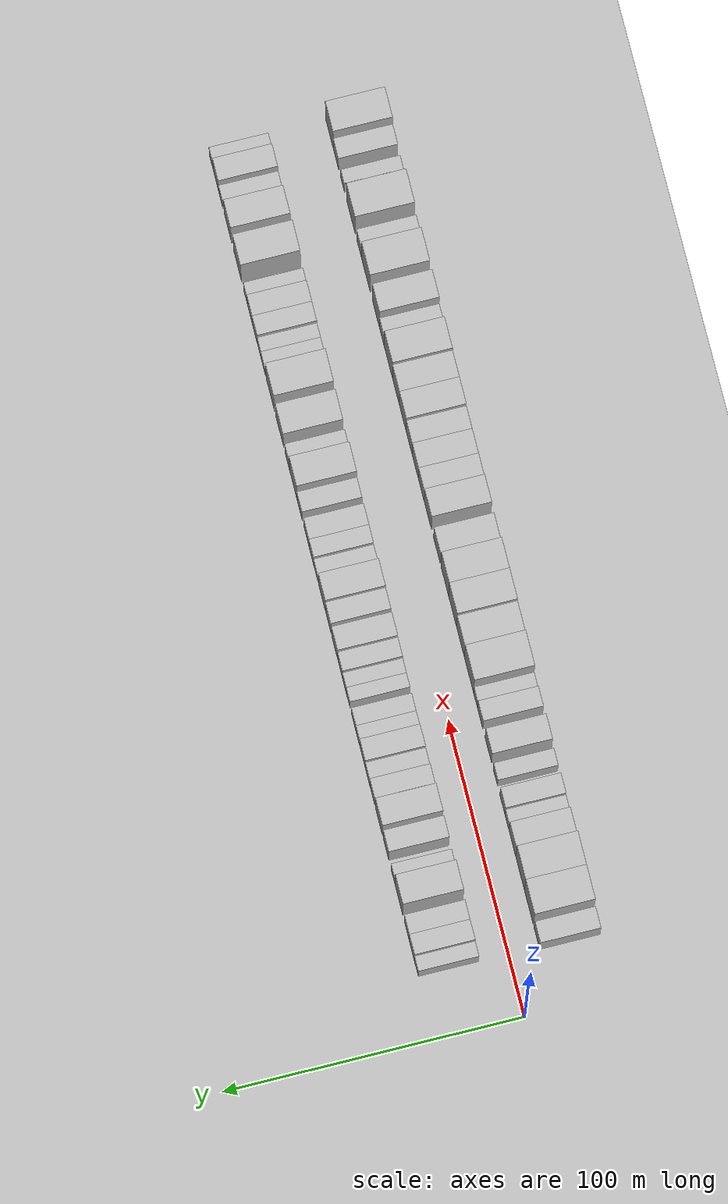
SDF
<?xml version="1.0" encoding="utf-8"?>

<sdf version="1.6">

   <world name="default">

      <gui fullscreen="0">

         <camera name="user_camera">

            <pose>-15 0 4.57585 0 0 0</pose>

            <view_controller>orbit</view_controller>

         </camera>

      </gui>

      <scene>

         <sky>

           <clouds>

             <speed>12</speed>

           </clouds>

         </sky>

         <ambient>0.4 0.4 0.4 1</ambient>

         <background>0.7 0.7 0.7 1</background>

         <shadows>1</shadows>

      </scene>

      <gravity>0 0 -9.8066</gravity>

      <magnetic_field>6e-06 2.3e-05 -4.2e-05</magnetic_field>

      <physics default="0" name="default_physics" type="ode">

         <ode>

            <solver>

               <type>quick</type>

               <iters>10</iters>

               <sor>1.0</sor>

               <use_dynamic_moi_rescaling>0</use_dynamic_moi_rescaling>

            </solver>

            <constraints>

               <cfm>0</cfm>

               <erp>0.2</erp>

               <contact_max_correcting_vel>100</contact_max_correcting_vel>

               <contact_surface_layer>0.001</contact_surface_layer>

            </constraints>

         </ode>

         <max_step_size>0.004</max_step_size>

         <real_time_factor>1</real_time_factor>

         <real_time_update_rate>250</real_time_update_rate>

      </physics>

      <light name="sun" type="directional">

         <cast_shadows>1</cast_shadows>

         <pose>0 0 10 0 0 0</pose>

         <diffuse>0.8 0.8 0.8 1</diffuse>

         <specular>0.2 0.2 0.2 1</specular>

         <attenuation>

            <range>1000</range>

            <constant>0.9</constant>

            <linear>0.01</linear>

            <quadratic>0.001</quadratic>

         </attenuation>

         <direction>-0.5 0.1 -0.9</direction>

      </light>

      <include>

         <name>ground_plane_1</name>

         <uri>model://HANNAS_ground_plane</uri>

         <pose>0 0 0  0 0 0</pose>

      </include>

      <include>

         <name>ground_plane_2</name>

         <uri>model://HANNAS_ground_plane</uri>

         <pose>100 0 0  0 0 0</pose>

      </include>

      <model name="building_1">

         <static>1</static>

         <pose frame="">23.5452 20.0000 0 0.000000 0.000000 1.570796</pose>

         <link name="link">

            <pose frame="">0 0 6.00 0 0 0</pose>

            <collision name="collision">

               <geometry>

                  <box>

                     <size>20.0000 5.0905 12.0000</size>

                  </box>

               </geometry>

               <max_contacts>10</max_contacts>

               <surface>

                  <contact>

                     <ode/>

                  </contact>

                  <bounce/>

                  <friction>

                     <torsional>

                        <ode/>

                     </torsional>

                     <ode/>

                  </friction>

               </surface>

            </collision>

            <visual name="visual">

               <cast_shadows>0</cast_shadows>

               <geometry>

                  <box>

                     <size>20.0000 5.0905 12.0000</size>

                  </box>

               </geometry>

               <material>

                  <script>

                     <uri>model://HANNAS_wall/materials/scripts</uri>

                     <uri>model://HANNAS_wall/materials/textures</uri>

                     <name>vrc/HANNAS_wall</name>

                  </script>

               </material>

            </visual>

            <self_collide>0</self_collide>

            <enable_wind>0</enable_wind>

            <kinematic>0</kinematic>

         </link>

      </model>

      <model name="building_2">

         <static>1</static>

         <pose frame="">29.5083 20.0000 0 0.000000 0.000000 1.570796</pose>

         <link name="link">

            <pose frame="">0 0 7.50 0 0 0</pose>

            <collision name="collision">

               <geometry>

                  <box>

                     <size>20.0000 6.8357 15.0000</size>

                  </box>

               </geometry>

               <max_contacts>10</max_contacts>

               <surface>

                  <contact>

                     <ode/>

                  </contact>

                  <bounce/>

                  <friction>

                     <torsional>

                        <ode/>

                     </torsional>

                     <ode/>

                  </friction>

               </surface>

            </collision>

            <visual name="visual">

               <cast_shadows>0</cast_shadows>

               <geometry>

                  <box>

                     <size>20.0000 6.8357 15.0000</size>

                  </box>

               </geometry>

               <material>

                  <script>

                     <uri>model://HANNAS_wall/materials/scripts</uri>

                     <uri>model://HANNAS_wall/materials/textures</uri>

                     <name>vrc/HANNAS_wall</name>

                  </script>

               </material>

            </visual>

            <self_collide>0</self_collide>

            <enable_wind>0</enable_wind>

            <kinematic>0</kinematic>

         </link>

      </model>

      <model name="building_3">

         <static>1</static>

         <pose frame="">36.2058 20.0000 0 0.000000 0.000000 1.570796</pose>

         <link name="link">

            <pose frame="">0 0 7.50 0 0 0</pose>

            <collision name="collision">

               <geometry>

                  <box>

                     <size>20.0000 6.5593 15.0000</size>

                  </box>

               </geometry>

               <max_contacts>10</max_contacts>

               <surface>

                  <contact>

                     <ode/>

                  </contact>

                  <bounce/>

                  <friction>

                     <torsional>

                        <ode/>

                     </torsional>

                     <ode/>

                  </friction>

               </surface>

            </collision>

            <visual name="visual">

               <cast_shadows>0</cast_shadows>

               <geometry>

                  <box>

                     <size>20.0000 6.5593 15.0000</size>

                  </box>

               </geometry>

               <material>

                  <script>

                     <uri>model://HANNAS_wall/materials/scripts</uri>

                     <uri>model://HANNAS_wall/materials/textures</uri>

                     <name>vrc/HANNAS_wall</name>

                  </script>

               </material>

            </visual>

            <self_collide>0</self_collide>

            <enable_wind>0</enable_wind>

            <kinematic>0</kinematic>

         </link>

      </model>

      <model name="building_4">

         <static>1</static>

         <pose frame="">46.4267 20.0000 0 0.000000 0.000000 1.570796</pose>

         <link name="link">

            <pose frame="">0 0 12.00 0 0 0</pose>

            <collision name="collision">

               <geometry>

                  <box>

                     <size>20.0000 9.8826 24.0000</size>

                  </box>

               </geometry>

               <max_contacts>10</max_contacts>

               <surface>

                  <contact>

                     <ode/>

                  </contact>

                  <bounce/>

                  <friction>

                     <torsional>

                        <ode/>

                     </torsional>

                     <ode/>

                  </friction>

               </surface>

            </collision>

            <visual name="visual">

               <cast_shadows>0</cast_shadows>

               <geometry>

                  <box>

                     <size>20.0000 9.8826 24.0000</size>

                  </box>

               </geometry>

               <material>

                  <script>

                     <uri>model://HANNAS_wall/materials/scripts</uri>

                     <uri>model://HANNAS_wall/materials/textures</uri>

                     <name>vrc/HANNAS_wall</name>

                  </script>

               </material>

            </visual>

            <self_collide>0</self_collide>

            <enable_wind>0</enable_wind>

            <kinematic>0</kinematic>

         </link>

      </model>

      <model name="building_5">

         <static>1</static>

         <pose frame="">54.1531 20.0000 0 0.000000 0.000000 1.570796</pose>

         <link name="link">

            <pose frame="">0 0 6.00 0 0 0</pose>

            <collision name="collision">

               <geometry>

                  <box>

                     <size>20.0000 5.5703 12.0000</size>

                  </box>

               </geometry>

               <max_contacts>10</max_contacts>

               <surface>

                  <contact>

                     <ode/>

                  </contact>

                  <bounce/>

                  <friction>

                     <torsional>

                        <ode/>

                     </torsional>

                     <ode/>

                  </friction>

               </surface>

            </collision>

            <visual name="visual">

               <cast_shadows>0</cast_shadows>

               <geometry>

                  <box>

                     <size>20.0000 5.5703 12.0000</size>

                  </box>

               </geometry>

               <material>

                  <script>

                     <uri>model://HANNAS_wall/materials/scripts</uri>

                     <uri>model://HANNAS_wall/materials/textures</uri>

                     <name>vrc/HANNAS_wall</name>

                  </script>

               </material>

            </visual>

            <self_collide>0</self_collide>

            <enable_wind>0</enable_wind>

            <kinematic>0</kinematic>

         </link>

      </model>

      <model name="building_6">

         <static>1</static>

         <pose frame="">63.5615 20.0000 0 0.000000 0.000000 1.570796</pose>

         <link name="link">

            <pose frame="">0 0 9.00 0 0 0</pose>

            <collision name="collision">

               <geometry>

                  <box>

                     <size>20.0000 7.2466 18.0000</size>

                  </box>

               </geometry>

               <max_contacts>10</max_contacts>

               <surface>

                  <contact>

                     <ode/>

                  </contact>

                  <bounce/>

                  <friction>

                     <torsional>

                        <ode/>

                     </torsional>

                     <ode/>

                  </friction>

               </surface>

            </collision>

            <visual name="visual">

               <cast_shadows>0</cast_shadows>

               <geometry>

                  <box>

                     <size>20.0000 7.2466 18.0000</size>

                  </box>

               </geometry>

               <material>

                  <script>

                     <uri>model://HANNAS_wall/materials/scripts</uri>

                     <uri>model://HANNAS_wall/materials/textures</uri>

                     <name>vrc/HANNAS_wall</name>

                  </script>

               </material>

            </visual>

            <self_collide>0</self_collide>

            <enable_wind>0</enable_wind>

            <kinematic>0</kinematic>

         </link>

      </model>

      <model name="building_7">

         <static>1</static>

         <pose frame="">72.8070 20.0000 0 0.000000 0.000000 1.570796</pose>

         <link name="link">

            <pose frame="">0 0 10.50 0 0 0</pose>

            <collision name="collision">

               <geometry>

                  <box>

                     <size>20.0000 9.2444 21.0000</size>

                  </box>

               </geometry>

               <max_contacts>10</max_contacts>

               <surface>

                  <contact>

                     <ode/>

                  </contact>

                  <bounce/>

                  <friction>

                     <torsional>

                        <ode/>

                     </torsional>

                     <ode/>

                  </friction>

               </surface>

            </collision>

            <visual name="visual">

               <cast_shadows>0</cast_shadows>

               <geometry>

                  <box>

                     <size>20.0000 9.2444 21.0000</size>

                  </box>

               </geometry>

               <material>

                  <script>

                     <uri>model://HANNAS_wall/materials/scripts</uri>

                     <uri>model://HANNAS_wall/materials/textures</uri>

                     <name>vrc/HANNAS_wall</name>

                  </script>

               </material>

            </visual>

            <self_collide>0</self_collide>

            <enable_wind>0</enable_wind>

            <kinematic>0</kinematic>

         </link>

      </model>

      <model name="building_8">

         <static>1</static>

         <pose frame="">81.7254 20.0000 0 0.000000 0.000000 1.570796</pose>

         <link name="link">

            <pose frame="">0 0 7.50 0 0 0</pose>

            <collision name="collision">

               <geometry>

                  <box>

                     <size>20.0000 6.5924 15.0000</size>

                  </box>

               </geometry>

               <max_contacts>10</max_contacts>

               <surface>

                  <contact>

                     <ode/>

                  </contact>

                  <bounce/>

                  <friction>

                     <torsional>

                        <ode/>

                     </torsional>

                     <ode/>

                  </friction>

               </surface>

            </collision>

            <visual name="visual">

               <cast_shadows>0</cast_shadows>

               <geometry>

                  <box>

                     <size>20.0000 6.5924 15.0000</size>

                  </box>

               </geometry>

               <material>

                  <script>

                     <uri>model://HANNAS_wall/materials/scripts</uri>

                     <uri>model://HANNAS_wall/materials/textures</uri>

                     <name>vrc/HANNAS_wall</name>

                  </script>

               </material>

            </visual>

            <self_collide>0</self_collide>

            <enable_wind>0</enable_wind>

            <kinematic>0</kinematic>

         </link>

      </model>

      <model name="building_9">

         <static>1</static>

         <pose frame="">87.9942 20.0000 0 0.000000 0.000000 1.570796</pose>

         <link name="link">

            <pose frame="">0 0 6.00 0 0 0</pose>

            <collision name="collision">

               <geometry>

                  <box>

                     <size>20.0000 5.9452 12.0000</size>

                  </box>

               </geometry>

               <max_contacts>10</max_contacts>

               <surface>

                  <contact>

                     <ode/>

                  </contact>

                  <bounce/>

                  <friction>

                     <torsional>

                        <ode/>

                     </torsional>

                     <ode/>

                  </friction>

               </surface>

            </collision>

            <visual name="visual">

               <cast_shadows>0</cast_shadows>

               <geometry>

                  <box>

                     <size>20.0000 5.9452 12.0000</size>

                  </box>

               </geometry>

               <material>

                  <script>

                     <uri>model://HANNAS_wall/materials/scripts</uri>

                     <uri>model://HANNAS_wall/materials/textures</uri>

                     <name>vrc/HANNAS_wall</name>

                  </script>

               </material>

            </visual>

            <self_collide>0</self_collide>

            <enable_wind>0</enable_wind>

            <kinematic>0</kinematic>

         </link>

      </model>

      <model name="building_10">

         <static>1</static>

         <pose frame="">94.6655 20.0000 0 0.000000 0.000000 1.570796</pose>

         <link name="link">

            <pose frame="">0 0 7.50 0 0 0</pose>

            <collision name="collision">

               <geometry>

                  <box>

                     <size>20.0000 7.3974 15.0000</size>

                  </box>

               </geometry>

               <max_contacts>10</max_contacts>

               <surface>

                  <contact>

                     <ode/>

                  </contact>

                  <bounce/>

                  <friction>

                     <torsional>

                        <ode/>

                     </torsional>

                     <ode/>

                  </friction>

               </surface>

            </collision>

            <visual name="visual">

               <cast_shadows>0</cast_shadows>

               <geometry>

                  <box>

                     <size>20.0000 7.3974 15.0000</size>

                  </box>

               </geometry>

               <material>

                  <script>

                     <uri>model://HANNAS_wall/materials/scripts</uri>

                     <uri>model://HANNAS_wall/materials/textures</uri>

                     <name>vrc/HANNAS_wall</name>

                  </script>

               </material>

            </visual>

            <self_collide>0</self_collide>

            <enable_wind>0</enable_wind>

            <kinematic>0</kinematic>

         </link>

      </model>

      <model name="building_11">

         <static>1</static>

         <pose frame="">100.8746 20.0000 0 0.000000 0.000000 1.570796</pose>

         <link name="link">

            <pose frame="">0 0 6.00 0 0 0</pose>

            <collision name="collision">

               <geometry>

                  <box>

                     <size>20.0000 5.0209 12.0000</size>

                  </box>

               </geometry>

               <max_contacts>10</max_contacts>

               <surface>

                  <contact>

                     <ode/>

                  </contact>

                  <bounce/>

                  <friction>

                     <torsional>

                        <ode/>

                     </torsional>

                     <ode/>

                  </friction>

               </surface>

            </collision>

            <visual name="visual">

               <cast_shadows>0</cast_shadows>

               <geometry>

                  <box>

                     <size>20.0000 5.0209 12.0000</size>

                  </box>

               </geometry>

               <material>

                  <script>

                     <uri>model://HANNAS_wall/materials/scripts</uri>

                     <uri>model://HANNAS_wall/materials/textures</uri>

                     <name>vrc/HANNAS_wall</name>

                  </script>

               </material>

            </visual>

            <self_collide>0</self_collide>

            <enable_wind>0</enable_wind>

            <kinematic>0</kinematic>

         </link>

      </model>

      <model name="building_12">

         <static>1</static>

         <pose frame="">106.3806 20.0000 0 0.000000 0.000000 1.570796</pose>

         <link name="link">

            <pose frame="">0 0 6.00 0 0 0</pose>

            <collision name="collision">

               <geometry>

                  <box>

                     <size>20.0000 5.9910 12.0000</size>

                  </box>

               </geometry>

               <max_contacts>10</max_contacts>

               <surface>

                  <contact>

                     <ode/>

                  </contact>

                  <bounce/>

                  <friction>

                     <torsional>

                        <ode/>

                     </torsional>

                     <ode/>

                  </friction>

               </surface>

            </collision>

            <visual name="visual">

               <cast_shadows>0</cast_shadows>

               <geometry>

                  <box>

                     <size>20.0000 5.9910 12.0000</size>

                  </box>

               </geometry>

               <material>

                  <script>

                     <uri>model://HANNAS_wall/materials/scripts</uri>

                     <uri>model://HANNAS_wall/materials/textures</uri>

                     <name>vrc/HANNAS_wall</name>

                  </script>

               </material>

            </visual>

            <self_collide>0</self_collide>

            <enable_wind>0</enable_wind>

            <kinematic>0</kinematic>

         </link>

      </model>

      <model name="building_13">

         <static>1</static>

         <pose frame="">113.8148 20.0000 0 0.000000 0.000000 1.570796</pose>

         <link name="link">

            <pose frame="">0 0 6.00 0 0 0</pose>

            <collision name="collision">

               <geometry>

                  <box>

                     <size>20.0000 4.8773 12.0000</size>

                  </box>

               </geometry>

               <max_contacts>10</max_contacts>

               <surface>

                  <contact>

                     <ode/>

                  </contact>

                  <bounce/>

                  <friction>

                     <torsional>

                        <ode/>

                     </torsional>

                     <ode/>

                  </friction>

               </surface>

            </collision>

            <visual name="visual">

               <cast_shadows>0</cast_shadows>

               <geometry>

                  <box>

                     <size>20.0000 4.8773 12.0000</size>

                  </box>

               </geometry>

               <material>

                  <script>

                     <uri>model://HANNAS_wall/materials/scripts</uri>

                     <uri>model://HANNAS_wall/materials/textures</uri>

                     <name>vrc/HANNAS_wall</name>

                  </script>

               </material>

            </visual>

            <self_collide>0</self_collide>

            <enable_wind>0</enable_wind>

            <kinematic>0</kinematic>

         </link>

      </model>

      <model name="building_14">

         <static>1</static>

         <pose frame="">118.7198 20.0000 0 0.000000 0.000000 1.570796</pose>

         <link name="link">

            <pose frame="">0 0 6.00 0 0 0</pose>

            <collision name="collision">

               <geometry>

                  <box>

                     <size>20.0000 4.9327 12.0000</size>

                  </box>

               </geometry>

               <max_contacts>10</max_contacts>

               <surface>

                  <contact>

                     <ode/>

                  </contact>

                  <bounce/>

                  <friction>

                     <torsional>

                        <ode/>

                     </torsional>

                     <ode/>

                  </friction>

               </surface>

            </collision>

            <visual name="visual">

               <cast_shadows>0</cast_shadows>

               <geometry>

                  <box>

                     <size>20.0000 4.9327 12.0000</size>

                  </box>

               </geometry>

               <material>

                  <script>

                     <uri>model://HANNAS_wall/materials/scripts</uri>

                     <uri>model://HANNAS_wall/materials/textures</uri>

                     <name>vrc/HANNAS_wall</name>

                  </script>

               </material>

            </visual>

            <self_collide>0</self_collide>

            <enable_wind>0</enable_wind>

            <kinematic>0</kinematic>

         </link>

      </model>

      <model name="building_15">

         <static>1</static>

         <pose frame="">124.4185 20.0000 0 0.000000 0.000000 1.570796</pose>

         <link name="link">

            <pose frame="">0 0 7.50 0 0 0</pose>

            <collision name="collision">

               <geometry>

                  <box>

                     <size>20.0000 6.4647 15.0000</size>

                  </box>

               </geometry>

               <max_contacts>10</max_contacts>

               <surface>

                  <contact>

                     <ode/>

                  </contact>

                  <bounce/>

                  <friction>

                     <torsional>

                        <ode/>

                     </torsional>

                     <ode/>

                  </friction>

               </surface>

            </collision>

            <visual name="visual">

               <cast_shadows>0</cast_shadows>

               <geometry>

                  <box>

                     <size>20.0000 6.4647 15.0000</size>

                  </box>

               </geometry>

               <material>

                  <script>

                     <uri>model://HANNAS_wall/materials/scripts</uri>

                     <uri>model://HANNAS_wall/materials/textures</uri>

                     <name>vrc/HANNAS_wall</name>

                  </script>

               </material>

            </visual>

            <self_collide>0</self_collide>

            <enable_wind>0</enable_wind>

            <kinematic>0</kinematic>

         </link>

      </model>

      <model name="building_16">

         <static>1</static>

         <pose frame="">131.6639 20.0000 0 0.000000 0.000000 1.570796</pose>

         <link name="link">

            <pose frame="">0 0 9.00 0 0 0</pose>

            <collision name="collision">

               <geometry>

                  <box>

                     <size>20.0000 8.0261 18.0000</size>

                  </box>

               </geometry>

               <max_contacts>10</max_contacts>

               <surface>

                  <contact>

                     <ode/>

                  </contact>

                  <bounce/>

                  <friction>

                     <torsional>

                        <ode/>

                     </torsional>

                     <ode/>

                  </friction>

               </surface>

            </collision>

            <visual name="visual">

               <cast_shadows>0</cast_shadows>

               <geometry>

                  <box>

                     <size>20.0000 8.0261 18.0000</size>

                  </box>

               </geometry>

               <material>

                  <script>

                     <uri>model://HANNAS_wall/materials/scripts</uri>

                     <uri>model://HANNAS_wall/materials/textures</uri>

                     <name>vrc/HANNAS_wall</name>

                  </script>

               </material>

            </visual>

            <self_collide>0</self_collide>

            <enable_wind>0</enable_wind>

            <kinematic>0</kinematic>

         </link>

      </model>

      <model name="building_17">

         <static>1</static>

         <pose frame="">140.2846 20.0000 0 0.000000 0.000000 1.570796</pose>

         <link name="link">

            <pose frame="">0 0 9.00 0 0 0</pose>

            <collision name="collision">

               <geometry>

                  <box>

                     <size>20.0000 7.2153 18.0000</size>

                  </box>

               </geometry>

               <max_contacts>10</max_contacts>

               <surface>

                  <contact>

                     <ode/>

                  </contact>

                  <bounce/>

                  <friction>

                     <torsional>

                        <ode/>

                     </torsional>

                     <ode/>

                  </friction>

               </surface>

            </collision>

            <visual name="visual">

               <cast_shadows>0</cast_shadows>

               <geometry>

                  <box>

                     <size>20.0000 7.2153 18.0000</size>

                  </box>

               </geometry>

               <material>

                  <script>

                     <uri>model://HANNAS_wall/materials/scripts</uri>

                     <uri>model://HANNAS_wall/materials/textures</uri>

                     <name>vrc/HANNAS_wall</name>

                  </script>

               </material>

            </visual>

            <self_collide>0</self_collide>

            <enable_wind>0</enable_wind>

            <kinematic>0</kinematic>

         </link>

      </model>

      <model name="building_18">

         <static>1</static>

         <pose frame="">148.5197 20.0000 0 0.000000 0.000000 1.570796</pose>

         <link name="link">

            <pose frame="">0 0 10.50 0 0 0</pose>

            <collision name="collision">

               <geometry>

                  <box>

                     <size>20.0000 9.2550 21.0000</size>

                  </box>

               </geometry>

               <max_contacts>10</max_contacts>

               <surface>

                  <contact>

                     <ode/>

                  </contact>

                  <bounce/>

                  <friction>

                     <torsional>

                        <ode/>

                     </torsional>

                     <ode/>

                  </friction>

               </surface>

            </collision>

            <visual name="visual">

               <cast_shadows>0</cast_shadows>

               <geometry>

                  <box>

                     <size>20.0000 9.2550 21.0000</size>

                  </box>

               </geometry>

               <material>

                  <script>

                     <uri>model://HANNAS_wall/materials/scripts</uri>

                     <uri>model://HANNAS_wall/materials/textures</uri>

                     <name>vrc/HANNAS_wall</name>

                  </script>

               </material>

            </visual>

            <self_collide>0</self_collide>

            <enable_wind>0</enable_wind>

            <kinematic>0</kinematic>

         </link>

      </model>

      <model name="building_19">

         <static>1</static>

         <pose frame="">156.9476 20.0000 0 0.000000 0.000000 1.570796</pose>

         <link name="link">

            <pose frame="">0 0 6.00 0 0 0</pose>

            <collision name="collision">

               <geometry>

                  <box>

                     <size>20.0000 5.6008 12.0000</size>

                  </box>

               </geometry>

               <max_contacts>10</max_contacts>

               <surface>

                  <contact>

                     <ode/>

                  </contact>

                  <bounce/>

                  <friction>

                     <torsional>

                        <ode/>

                     </torsional>

                     <ode/>

                  </friction>

               </surface>

            </collision>

            <visual name="visual">

               <cast_shadows>0</cast_shadows>

               <geometry>

                  <box>

                     <size>20.0000 5.6008 12.0000</size>

                  </box>

               </geometry>

               <material>

                  <script>

                     <uri>model://HANNAS_wall/materials/scripts</uri>

                     <uri>model://HANNAS_wall/materials/textures</uri>

                     <name>vrc/HANNAS_wall</name>

                  </script>

               </material>

            </visual>

            <self_collide>0</self_collide>

            <enable_wind>0</enable_wind>

            <kinematic>0</kinematic>

         </link>

      </model>

      <model name="building_20">

         <static>1</static>

         <pose frame="">162.8189 20.0000 0 0.000000 0.000000 1.570796</pose>

         <link name="link">

            <pose frame="">0 0 7.50 0 0 0</pose>

            <collision name="collision">

               <geometry>

                  <box>

                     <size>20.0000 6.1417 15.0000</size>

                  </box>

               </geometry>

               <max_contacts>10</max_contacts>

               <surface>

                  <contact>

                     <ode/>

                  </contact>

                  <bounce/>

                  <friction>

                     <torsional>

                        <ode/>

                     </torsional>

                     <ode/>

                  </friction>

               </surface>

            </collision>

            <visual name="visual">

               <cast_shadows>0</cast_shadows>

               <geometry>

                  <box>

                     <size>20.0000 6.1417 15.0000</size>

                  </box>

               </geometry>

               <material>

                  <script>

                     <uri>model://HANNAS_wall/materials/scripts</uri>

                     <uri>model://HANNAS_wall/materials/textures</uri>

                     <name>vrc/HANNAS_wall</name>

                  </script>

               </material>

            </visual>

            <self_collide>0</self_collide>

            <enable_wind>0</enable_wind>

            <kinematic>0</kinematic>

         </link>

      </model>

      <model name="building_21">

         <static>1</static>

         <pose frame="">169.5122 20.0000 0 0.000000 0.000000 1.570796</pose>

         <link name="link">

            <pose frame="">0 0 7.50 0 0 0</pose>

            <collision name="collision">

               <geometry>

                  <box>

                     <size>20.0000 7.2449 15.0000</size>

                  </box>

               </geometry>

               <max_contacts>10</max_contacts>

               <surface>

                  <contact>

                     <ode/>

                  </contact>

                  <bounce/>

                  <friction>

                     <torsional>

                        <ode/>

                     </torsional>

                     <ode/>

                  </friction>

               </surface>

            </collision>

            <visual name="visual">

               <cast_shadows>0</cast_shadows>

               <geometry>

                  <box>

                     <size>20.0000 7.2449 15.0000</size>

                  </box>

               </geometry>

               <material>

                  <script>

                     <uri>model://HANNAS_wall/materials/scripts</uri>

                     <uri>model://HANNAS_wall/materials/textures</uri>

                     <name>vrc/HANNAS_wall</name>

                  </script>

               </material>

            </visual>

            <self_collide>0</self_collide>

            <enable_wind>0</enable_wind>

            <kinematic>0</kinematic>

         </link>

      </model>

      <model name="building_22">

         <static>1</static>

         <pose frame="">178.5858 20.0000 0 0.000000 0.000000 1.570796</pose>

         <link name="link">

            <pose frame="">0 0 7.50 0 0 0</pose>

            <collision name="collision">

               <geometry>

                  <box>

                     <size>20.0000 6.9025 15.0000</size>

                  </box>

               </geometry>

               <max_contacts>10</max_contacts>

               <surface>

                  <contact>

                     <ode/>

                  </contact>

                  <bounce/>

                  <friction>

                     <torsional>

                        <ode/>

                     </torsional>

                     <ode/>

                  </friction>

               </surface>

            </collision>

            <visual name="visual">

               <cast_shadows>0</cast_shadows>

               <geometry>

                  <box>

                     <size>20.0000 6.9025 15.0000</size>

                  </box>

               </geometry>

               <material>

                  <script>

                     <uri>model://HANNAS_wall/materials/scripts</uri>

                     <uri>model://HANNAS_wall/materials/textures</uri>

                     <name>vrc/HANNAS_wall</name>

                  </script>

               </material>

            </visual>

            <self_collide>0</self_collide>

            <enable_wind>0</enable_wind>

            <kinematic>0</kinematic>

         </link>

      </model>

      <model name="building_23">

         <static>1</static>

         <pose frame="">187.1096 20.0000 0 0.000000 0.000000 1.570796</pose>

         <link name="link">

            <pose frame="">0 0 12.00 0 0 0</pose>

            <collision name="collision">

               <geometry>

                  <box>

                     <size>20.0000 10.1450 24.0000</size>

                  </box>

               </geometry>

               <max_contacts>10</max_contacts>

               <surface>

                  <contact>

                     <ode/>

                  </contact>

                  <bounce/>

                  <friction>

                     <torsional>

                        <ode/>

                     </torsional>

                     <ode/>

                  </friction>

               </surface>

            </collision>

            <visual name="visual">

               <cast_shadows>0</cast_shadows>

               <geometry>

                  <box>

                     <size>20.0000 10.1450 24.0000</size>

                  </box>

               </geometry>

               <material>

                  <script>

                     <uri>model://HANNAS_wall/materials/scripts</uri>

                     <uri>model://HANNAS_wall/materials/textures</uri>

                     <name>vrc/HANNAS_wall</name>

                  </script>

               </material>

            </visual>

            <self_collide>0</self_collide>

            <enable_wind>0</enable_wind>

            <kinematic>0</kinematic>

         </link>

      </model>

      <model name="building_24">

         <static>1</static>

         <pose frame="">195.2996 20.0000 0 0.000000 0.000000 1.570796</pose>

         <link name="link">

            <pose frame="">0 0 7.50 0 0 0</pose>

            <collision name="collision">

               <geometry>

                  <box>

                     <size>20.0000 6.2351 15.0000</size>

                  </box>

               </geometry>

               <max_contacts>10</max_contacts>

               <surface>

                  <contact>

                     <ode/>

                  </contact>

                  <bounce/>

                  <friction>

                     <torsional>

                        <ode/>

                     </torsional>

                     <ode/>

                  </friction>

               </surface>

            </collision>

            <visual name="visual">

               <cast_shadows>0</cast_shadows>

               <geometry>

                  <box>

                     <size>20.0000 6.2351 15.0000</size>

                  </box>

               </geometry>

               <material>

                  <script>

                     <uri>model://HANNAS_wall/materials/scripts</uri>

                     <uri>model://HANNAS_wall/materials/textures</uri>

                     <name>vrc/HANNAS_wall</name>

                  </script>

               </material>

            </visual>

            <self_collide>0</self_collide>

            <enable_wind>0</enable_wind>

            <kinematic>0</kinematic>

         </link>

      </model>

      <model name="building_25">

         <static>1</static>

         <pose frame="">205.6078 20.0000 0 0.000000 0.000000 1.570796</pose>

         <link name="link">

            <pose frame="">0 0 10.50 0 0 0</pose>

            <collision name="collision">

               <geometry>

                  <box>

                     <size>20.0000 10.3812 21.0000</size>

                  </box>

               </geometry>

               <max_contacts>10</max_contacts>

               <surface>

                  <contact>

                     <ode/>

                  </contact>

                  <bounce/>

                  <friction>

                     <torsional>

                        <ode/>

                     </torsional>

                     <ode/>

                  </friction>

               </surface>

            </collision>

            <visual name="visual">

               <cast_shadows>0</cast_shadows>

               <geometry>

                  <box>

                     <size>20.0000 10.3812 21.0000</size>

                  </box>

               </geometry>

               <material>

                  <script>

                     <uri>model://HANNAS_wall/materials/scripts</uri>

                     <uri>model://HANNAS_wall/materials/textures</uri>

                     <name>vrc/HANNAS_wall</name>

                  </script>

               </material>

            </visual>

            <self_collide>0</self_collide>

            <enable_wind>0</enable_wind>

            <kinematic>0</kinematic>

         </link>

      </model>

      <model name="building_26">

         <static>1</static>

         <pose frame="">218.3820 20.0000 0 0.000000 0.000000 1.570796</pose>

         <link name="link">

            <pose frame="">0 0 12.00 0 0 0</pose>

            <collision name="collision">

               <geometry>

                  <box>

                     <size>20.0000 11.1672 24.0000</size>

                  </box>

               </geometry>

               <max_contacts>10</max_contacts>

               <surface>

                  <contact>

                     <ode/>

                  </contact>

                  <bounce/>

                  <friction>

                     <torsional>

                        <ode/>

                     </torsional>

                     <ode/>

                  </friction>

               </surface>

            </collision>

            <visual name="visual">

               <cast_shadows>0</cast_shadows>

               <geometry>

                  <box>

                     <size>20.0000 11.1672 24.0000</size>

                  </box>

               </geometry>

               <material>

                  <script>

                     <uri>model://HANNAS_wall/materials/scripts</uri>

                     <uri>model://HANNAS_wall/materials/textures</uri>

                     <name>vrc/HANNAS_wall</name>

                  </script>

               </material>

            </visual>

            <self_collide>0</self_collide>

            <enable_wind>0</enable_wind>

            <kinematic>0</kinematic>

         </link>

      </model>

      <model name="building_27">

         <static>1</static>

         <pose frame="">227.8419 20.0000 0 0.000000 0.000000 1.570796</pose>

         <link name="link">

            <pose frame="">0 0 6.00 0 0 0</pose>

            <collision name="collision">

               <geometry>

                  <box>

                     <size>20.0000 5.7525 12.0000</size>

                  </box>

               </geometry>

               <max_contacts>10</max_contacts>

               <surface>

                  <contact>

                     <ode/>

                  </contact>

                  <bounce/>

                  <friction>

                     <torsional>

                        <ode/>

                     </torsional>

                     <ode/>

                  </friction>

               </surface>

            </collision>

            <visual name="visual">

               <cast_shadows>0</cast_shadows>

               <geometry>

                  <box>

                     <size>20.0000 5.7525 12.0000</size>

                  </box>

               </geometry>

               <material>

                  <script>

                     <uri>model://HANNAS_wall/materials/scripts</uri>

                     <uri>model://HANNAS_wall/materials/textures</uri>

                     <name>vrc/HANNAS_wall</name>

                  </script>

               </material>

            </visual>

            <self_collide>0</self_collide>

            <enable_wind>0</enable_wind>

            <kinematic>0</kinematic>

         </link>

      </model>

      <model name="building_28">

         <static>1</static>

         <pose frame="">233.1549 20.0000 0 0.000000 0.000000 1.570796</pose>

         <link name="link">

            <pose frame="">0 0 6.00 0 0 0</pose>

            <collision name="collision">

               <geometry>

                  <box>

                     <size>20.0000 4.8735 12.0000</size>

                  </box>

               </geometry>

               <max_contacts>10</max_contacts>

               <surface>

                  <contact>

                     <ode/>

                  </contact>

                  <bounce/>

                  <friction>

                     <torsional>

                        <ode/>

                     </torsional>

                     <ode/>

                  </friction>

               </surface>

            </collision>

            <visual name="visual">

               <cast_shadows>0</cast_shadows>

               <geometry>

                  <box>

                     <size>20.0000 4.8735 12.0000</size>

                  </box>

               </geometry>

               <material>

                  <script>

                     <uri>model://HANNAS_wall/materials/scripts</uri>

                     <uri>model://HANNAS_wall/materials/textures</uri>

                     <name>vrc/HANNAS_wall</name>

                  </script>

               </material>

            </visual>

            <self_collide>0</self_collide>

            <enable_wind>0</enable_wind>

            <kinematic>0</kinematic>

         </link>

      </model>

      <model name="building_29">

         <static>1</static>

         <pose frame="">238.9770 20.0000 0 0.000000 0.000000 1.570796</pose>

         <link name="link">

            <pose frame="">0 0 7.50 0 0 0</pose>

            <collision name="collision">

               <geometry>

                  <box>

                     <size>20.0000 6.7708 15.0000</size>

                  </box>

               </geometry>

               <max_contacts>10</max_contacts>

               <surface>

                  <contact>

                     <ode/>

                  </contact>

                  <bounce/>

                  <friction>

                     <torsional>

                        <ode/>

                     </torsional>

                     <ode/>

                  </friction>

               </surface>

            </collision>

            <visual name="visual">

               <cast_shadows>0</cast_shadows>

               <geometry>

                  <box>

                     <size>20.0000 6.7708 15.0000</size>

                  </box>

               </geometry>

               <material>

                  <script>

                     <uri>model://HANNAS_wall/materials/scripts</uri>

                     <uri>model://HANNAS_wall/materials/textures</uri>

                     <name>vrc/HANNAS_wall</name>

                  </script>

               </material>

            </visual>

            <self_collide>0</self_collide>

            <enable_wind>0</enable_wind>

            <kinematic>0</kinematic>

         </link>

      </model>

      <model name="building_30">

         <static>1</static>

         <pose frame="">245.9957 20.0000 0 0.000000 0.000000 1.570796</pose>

         <link name="link">

            <pose frame="">0 0 7.50 0 0 0</pose>

            <collision name="collision">

               <geometry>

                  <box>

                     <size>20.0000 7.2665 15.0000</size>

                  </box>

               </geometry>

               <max_contacts>10</max_contacts>

               <surface>

                  <contact>

                     <ode/>

                  </contact>

                  <bounce/>

                  <friction>

                     <torsional>

                        <ode/>

                     </torsional>

                     <ode/>

                  </friction>

               </surface>

            </collision>

            <visual name="visual">

               <cast_shadows>0</cast_shadows>

               <geometry>

                  <box>

                     <size>20.0000 7.2665 15.0000</size>

                  </box>

               </geometry>

               <material>

                  <script>

                     <uri>model://HANNAS_wall/materials/scripts</uri>

                     <uri>model://HANNAS_wall/materials/textures</uri>

                     <name>vrc/HANNAS_wall</name>

                  </script>

               </material>

            </visual>

            <self_collide>0</self_collide>

            <enable_wind>0</enable_wind>

            <kinematic>0</kinematic>

         </link>

      </model>

      <model name="building_31">

         <static>1</static>

         <pose frame="">252.1011 20.0000 0 0.000000 0.000000 1.570796</pose>

         <link name="link">

            <pose frame="">0 0 6.00 0 0 0</pose>

            <collision name="collision">

               <geometry>

                  <box>

                     <size>20.0000 4.9444 12.0000</size>

                  </box>

               </geometry>

               <max_contacts>10</max_contacts>

               <surface>

                  <contact>

                     <ode/>

                  </contact>

                  <bounce/>

                  <friction>

                     <torsional>

                        <ode/>

                     </torsional>

                     <ode/>

                  </friction>

               </surface>

            </collision>

            <visual name="visual">

               <cast_shadows>0</cast_shadows>

               <geometry>

                  <box>

                     <size>20.0000 4.9444 12.0000</size>

                  </box>

               </geometry>

               <material>

                  <script>

                     <uri>model://HANNAS_wall/materials/scripts</uri>

                     <uri>model://HANNAS_wall/materials/textures</uri>

                     <name>vrc/HANNAS_wall</name>

                  </script>

               </material>

            </visual>

            <self_collide>0</self_collide>

            <enable_wind>0</enable_wind>

            <kinematic>0</kinematic>

         </link>

      </model>

      <model name="building_32">

         <static>1</static>

         <pose frame="">262.8687 20.0000 0 0.000000 0.000000 1.570796</pose>

         <link name="link">

            <pose frame="">0 0 12.00 0 0 0</pose>

            <collision name="collision">

               <geometry>

                  <box>

                     <size>20.0000 10.5908 24.0000</size>

                  </box>

               </geometry>

               <max_contacts>10</max_contacts>

               <surface>

                  <contact>

                     <ode/>

                  </contact>

                  <bounce/>

                  <friction>

                     <torsional>

                        <ode/>

                     </torsional>

                     <ode/>

                  </friction>

               </surface>

            </collision>

            <visual name="visual">

               <cast_shadows>0</cast_shadows>

               <geometry>

                  <box>

                     <size>20.0000 10.5908 24.0000</size>

                  </box>

               </geometry>

               <material>

                  <script>

                     <uri>model://HANNAS_wall/materials/scripts</uri>

                     <uri>model://HANNAS_wall/materials/textures</uri>

                     <name>vrc/HANNAS_wall</name>

                  </script>

               </material>

            </visual>

            <self_collide>0</self_collide>

            <enable_wind>0</enable_wind>

            <kinematic>0</kinematic>

         </link>

      </model>

      <model name="building_33">

         <static>1</static>

         <pose frame="">276.0314 20.0000 0 0.000000 0.000000 1.570796</pose>

         <link name="link">

            <pose frame="">0 0 10.50 0 0 0</pose>

            <collision name="collision">

               <geometry>

                  <box>

                     <size>20.0000 9.7345 21.0000</size>

                  </box>

               </geometry>

               <max_contacts>10</max_contacts>

               <surface>

                  <contact>

                     <ode/>

                  </contact>

                  <bounce/>

                  <friction>

                     <torsional>

                        <ode/>

                     </torsional>

                     <ode/>

                  </friction>

               </surface>

            </collision>

            <visual name="visual">

               <cast_shadows>0</cast_shadows>

               <geometry>

                  <box>

                     <size>20.0000 9.7345 21.0000</size>

                  </box>

               </geometry>

               <material>

                  <script>

                     <uri>model://HANNAS_wall/materials/scripts</uri>

                     <uri>model://HANNAS_wall/materials/textures</uri>

                     <name>vrc/HANNAS_wall</name>

                  </script>

               </material>

            </visual>

            <self_collide>0</self_collide>

            <enable_wind>0</enable_wind>

            <kinematic>0</kinematic>

         </link>

      </model>

      <model name="building_34">

         <static>1</static>

         <pose frame="">285.5381 20.0000 0 0.000000 0.000000 1.570796</pose>

         <link name="link">

            <pose frame="">0 0 6.00 0 0 0</pose>

            <collision name="collision">

               <geometry>

                  <box>

                     <size>20.0000 5.2789 12.0000</size>

                  </box>

               </geometry>

               <max_contacts>10</max_contacts>

               <surface>

                  <contact>

                     <ode/>

                  </contact>

                  <bounce/>

                  <friction>

                     <torsional>

                        <ode/>

                     </torsional>

                     <ode/>

                  </friction>

               </surface>

            </collision>

            <visual name="visual">

               <cast_shadows>0</cast_shadows>

               <geometry>

                  <box>

                     <size>20.0000 5.2789 12.0000</size>

                  </box>

               </geometry>

               <material>

                  <script>

                     <uri>model://HANNAS_wall/materials/scripts</uri>

                     <uri>model://HANNAS_wall/materials/textures</uri>

                     <name>vrc/HANNAS_wall</name>

                  </script>

               </material>

            </visual>

            <self_collide>0</self_collide>

            <enable_wind>0</enable_wind>

            <kinematic>0</kinematic>

         </link>

      </model>

      <model name="building_35">

         <static>1</static>

         <pose frame="">292.1135 20.0000 0 0.000000 0.000000 1.570796</pose>

         <link name="link">

            <pose frame="">0 0 9.00 0 0 0</pose>

            <collision name="collision">

               <geometry>

                  <box>

                     <size>20.0000 7.8719 18.0000</size>

                  </box>

               </geometry>

               <max_contacts>10</max_contacts>

               <surface>

                  <contact>

                     <ode/>

                  </contact>

                  <bounce/>

                  <friction>

                     <torsional>

                        <ode/>

                     </torsional>

                     <ode/>

                  </friction>

               </surface>

            </collision>

            <visual name="visual">

               <cast_shadows>0</cast_shadows>

               <geometry>

                  <box>

                     <size>20.0000 7.8719 18.0000</size>

                  </box>

               </geometry>

               <material>

                  <script>

                     <uri>model://HANNAS_wall/materials/scripts</uri>

                     <uri>model://HANNAS_wall/materials/textures</uri>

                     <name>vrc/HANNAS_wall</name>

                  </script>

               </material>

            </visual>

            <self_collide>0</self_collide>

            <enable_wind>0</enable_wind>

            <kinematic>0</kinematic>

         </link>

      </model>

      <model name="building_36">

         <static>1</static>

         <pose frame="">298.7198 20.0000 0 0.000000 0.000000 1.570796</pose>

         <link name="link">

            <pose frame="">0 0 6.00 0 0 0</pose>

            <collision name="collision">

               <geometry>

                  <box>

                     <size>20.0000 5.3409 12.0000</size>

                  </box>

               </geometry>

               <max_contacts>10</max_contacts>

               <surface>

                  <contact>

                     <ode/>

                  </contact>

                  <bounce/>

                  <friction>

                     <torsional>

                        <ode/>

                     </torsional>

                     <ode/>

                  </friction>

               </surface>

            </collision>

            <visual name="visual">

               <cast_shadows>0</cast_shadows>

               <geometry>

                  <box>

                     <size>20.0000 5.3409 12.0000</size>

                  </box>

               </geometry>

               <material>

                  <script>

                     <uri>model://HANNAS_wall/materials/scripts</uri>

                     <uri>model://HANNAS_wall/materials/textures</uri>

                     <name>vrc/HANNAS_wall</name>

                  </script>

               </material>

            </visual>

            <self_collide>0</self_collide>

            <enable_wind>0</enable_wind>

            <kinematic>0</kinematic>

         </link>

      </model>

      <model name="building_37">

         <static>1</static>

         <pose frame="">23.5860 -20.0000 0 0.000000 0.000000 1.570796</pose>

         <link name="link">

            <pose frame="">0 0 7.50 0 0 0</pose>

            <collision name="collision">

               <geometry>

                  <box>

                     <size>20.0000 7.1719 15.0000</size>

                  </box>

               </geometry>

               <max_contacts>10</max_contacts>

               <surface>

                  <contact>

                     <ode/>

                  </contact>

                  <bounce/>

                  <friction>

                     <torsional>

                        <ode/>

                     </torsional>

                     <ode/>

                  </friction>

               </surface>

            </collision>

            <visual name="visual">

               <cast_shadows>0</cast_shadows>

               <geometry>

                  <box>

                     <size>20.0000 7.1719 15.0000</size>

                  </box>

               </geometry>

               <material>

                  <script>

                     <uri>model://HANNAS_wall/materials/scripts</uri>

                     <uri>model://HANNAS_wall/materials/textures</uri>

                     <name>vrc/HANNAS_wall</name>

                  </script>

               </material>

            </visual>

            <self_collide>0</self_collide>

            <enable_wind>0</enable_wind>

            <kinematic>0</kinematic>

         </link>

      </model>

      <model name="building_38">

         <static>1</static>

         <pose frame="">33.9682 -20.0000 0 0.000000 0.000000 1.570796</pose>

         <link name="link">

            <pose frame="">0 0 12.00 0 0 0</pose>

            <collision name="collision">

               <geometry>

                  <box>

                     <size>20.0000 11.5924 24.0000</size>

                  </box>

               </geometry>

               <max_contacts>10</max_contacts>

               <surface>

                  <contact>

                     <ode/>

                  </contact>

                  <bounce/>

                  <friction>

                     <torsional>

                        <ode/>

                     </torsional>

                     <ode/>

                  </friction>

               </surface>

            </collision>

            <visual name="visual">

               <cast_shadows>0</cast_shadows>

               <geometry>

                  <box>

                     <size>20.0000 11.5924 24.0000</size>

                  </box>

               </geometry>

               <material>

                  <script>

                     <uri>model://HANNAS_wall/materials/scripts</uri>

                     <uri>model://HANNAS_wall/materials/textures</uri>

                     <name>vrc/HANNAS_wall</name>

                  </script>

               </material>

            </visual>

            <self_collide>0</self_collide>

            <enable_wind>0</enable_wind>

            <kinematic>0</kinematic>

         </link>

      </model>

      <model name="building_39">

         <static>1</static>

         <pose frame="">45.3698 -20.0000 0 0.000000 0.000000 1.570796</pose>

         <link name="link">

            <pose frame="">0 0 12.00 0 0 0</pose>

            <collision name="collision">

               <geometry>

                  <box>

                     <size>20.0000 11.2108 24.0000</size>

                  </box>

               </geometry>

               <max_contacts>10</max_contacts>

               <surface>

                  <contact>

                     <ode/>

                  </contact>

                  <bounce/>

                  <friction>

                     <torsional>

                        <ode/>

                     </torsional>

                     <ode/>

                  </friction>

               </surface>

            </collision>

            <visual name="visual">

               <cast_shadows>0</cast_shadows>

               <geometry>

                  <box>

                     <size>20.0000 11.2108 24.0000</size>

                  </box>

               </geometry>

               <material>

                  <script>

                     <uri>model://HANNAS_wall/materials/scripts</uri>

                     <uri>model://HANNAS_wall/materials/textures</uri>

                     <name>vrc/HANNAS_wall</name>

                  </script>

               </material>

            </visual>

            <self_collide>0</self_collide>

            <enable_wind>0</enable_wind>

            <kinematic>0</kinematic>

         </link>

      </model>

      <model name="building_40">

         <static>1</static>

         <pose frame="">55.4457 -20.0000 0 0.000000 0.000000 1.570796</pose>

         <link name="link">

            <pose frame="">0 0 9.00 0 0 0</pose>

            <collision name="collision">

               <geometry>

                  <box>

                     <size>20.0000 8.9409 18.0000</size>

                  </box>

               </geometry>

               <max_contacts>10</max_contacts>

               <surface>

                  <contact>

                     <ode/>

                  </contact>

                  <bounce/>

                  <friction>

                     <torsional>

                        <ode/>

                     </torsional>

                     <ode/>

                  </friction>

               </surface>

            </collision>

            <visual name="visual">

               <cast_shadows>0</cast_shadows>

               <geometry>

                  <box>

                     <size>20.0000 8.9409 18.0000</size>

                  </box>

               </geometry>

               <material>

                  <script>

                     <uri>model://HANNAS_wall/materials/scripts</uri>

                     <uri>model://HANNAS_wall/materials/textures</uri>

                     <name>vrc/HANNAS_wall</name>

                  </script>

               </material>

            </visual>

            <self_collide>0</self_collide>

            <enable_wind>0</enable_wind>

            <kinematic>0</kinematic>

         </link>

      </model>

      <model name="building_41">

         <static>1</static>

         <pose frame="">62.4994 -20.0000 0 0.000000 0.000000 1.570796</pose>

         <link name="link">

            <pose frame="">0 0 6.00 0 0 0</pose>

            <collision name="collision">

               <geometry>

                  <box>

                     <size>20.0000 5.1665 12.0000</size>

                  </box>

               </geometry>

               <max_contacts>10</max_contacts>

               <surface>

                  <contact>

                     <ode/>

                  </contact>

                  <bounce/>

                  <friction>

                     <torsional>

                        <ode/>

                     </torsional>

                     <ode/>

                  </friction>

               </surface>

            </collision>

            <visual name="visual">

               <cast_shadows>0</cast_shadows>

               <geometry>

                  <box>

                     <size>20.0000 5.1665 12.0000</size>

                  </box>

               </geometry>

               <material>

                  <script>

                     <uri>model://HANNAS_wall/materials/scripts</uri>

                     <uri>model://HANNAS_wall/materials/textures</uri>

                     <name>vrc/HANNAS_wall</name>

                  </script>

               </material>

            </visual>

            <self_collide>0</self_collide>

            <enable_wind>0</enable_wind>

            <kinematic>0</kinematic>

         </link>

      </model>

      <model name="building_42">

         <static>1</static>

         <pose frame="">68.5233 -20.0000 0 0.000000 0.000000 1.570796</pose>

         <link name="link">

            <pose frame="">0 0 7.50 0 0 0</pose>

            <collision name="collision">

               <geometry>

                  <box>

                     <size>20.0000 6.8814 15.0000</size>

                  </box>

               </geometry>

               <max_contacts>10</max_contacts>

               <surface>

                  <contact>

                     <ode/>

                  </contact>

                  <bounce/>

                  <friction>

                     <torsional>

                        <ode/>

                     </torsional>

                     <ode/>

                  </friction>

               </surface>

            </collision>

            <visual name="visual">

               <cast_shadows>0</cast_shadows>

               <geometry>

                  <box>

                     <size>20.0000 6.8814 15.0000</size>

                  </box>

               </geometry>

               <material>

                  <script>

                     <uri>model://HANNAS_wall/materials/scripts</uri>

                     <uri>model://HANNAS_wall/materials/textures</uri>

                     <name>vrc/HANNAS_wall</name>

                  </script>

               </material>

            </visual>

            <self_collide>0</self_collide>

            <enable_wind>0</enable_wind>

            <kinematic>0</kinematic>

         </link>

      </model>

      <model name="building_43">

         <static>1</static>

         <pose frame="">77.8612 -20.0000 0 0.000000 0.000000 1.570796</pose>

         <link name="link">

            <pose frame="">0 0 6.00 0 0 0</pose>

            <collision name="collision">

               <geometry>

                  <box>

                     <size>20.0000 5.7943 12.0000</size>

                  </box>

               </geometry>

               <max_contacts>10</max_contacts>

               <surface>

                  <contact>

                     <ode/>

                  </contact>

                  <bounce/>

                  <friction>

                     <torsional>

                        <ode/>

                     </torsional>

                     <ode/>

                  </friction>

               </surface>

            </collision>

            <visual name="visual">

               <cast_shadows>0</cast_shadows>

               <geometry>

                  <box>

                     <size>20.0000 5.7943 12.0000</size>

                  </box>

               </geometry>

               <material>

                  <script>

                     <uri>model://HANNAS_wall/materials/scripts</uri>

                     <uri>model://HANNAS_wall/materials/textures</uri>

                     <name>vrc/HANNAS_wall</name>

                  </script>

               </material>

            </visual>

            <self_collide>0</self_collide>

            <enable_wind>0</enable_wind>

            <kinematic>0</kinematic>

         </link>

      </model>

      <model name="building_44">

         <static>1</static>

         <pose frame="">87.0350 -20.0000 0 0.000000 0.000000 1.570796</pose>

         <link name="link">

            <pose frame="">0 0 9.00 0 0 0</pose>

            <collision name="collision">

               <geometry>

                  <box>

                     <size>20.0000 8.5533 18.0000</size>

                  </box>

               </geometry>

               <max_contacts>10</max_contacts>

               <surface>

                  <contact>

                     <ode/>

                  </contact>

                  <bounce/>

                  <friction>

                     <torsional>

                        <ode/>

                     </torsional>

                     <ode/>

                  </friction>

               </surface>

            </collision>

            <visual name="visual">

               <cast_shadows>0</cast_shadows>

               <geometry>

                  <box>

                     <size>20.0000 8.5533 18.0000</size>

                  </box>

               </geometry>

               <material>

                  <script>

                     <uri>model://HANNAS_wall/materials/scripts</uri>

                     <uri>model://HANNAS_wall/materials/textures</uri>

                     <name>vrc/HANNAS_wall</name>

                  </script>

               </material>

            </visual>

            <self_collide>0</self_collide>

            <enable_wind>0</enable_wind>

            <kinematic>0</kinematic>

         </link>

      </model>

      <model name="building_45">

         <static>1</static>

         <pose frame="">97.7289 -20.0000 0 0.000000 0.000000 1.570796</pose>

         <link name="link">

            <pose frame="">0 0 7.50 0 0 0</pose>

            <collision name="collision">

               <geometry>

                  <box>

                     <size>20.0000 6.8347 15.0000</size>

                  </box>

               </geometry>

               <max_contacts>10</max_contacts>

               <surface>

                  <contact>

                     <ode/>

                  </contact>

                  <bounce/>

                  <friction>

                     <torsional>

                        <ode/>

                     </torsional>

                     <ode/>

                  </friction>

               </surface>

            </collision>

            <visual name="visual">

               <cast_shadows>0</cast_shadows>

               <geometry>

                  <box>

                     <size>20.0000 6.8347 15.0000</size>

                  </box>

               </geometry>

               <material>

                  <script>

                     <uri>model://HANNAS_wall/materials/scripts</uri>

                     <uri>model://HANNAS_wall/materials/textures</uri>

                     <name>vrc/HANNAS_wall</name>

                  </script>

               </material>

            </visual>

            <self_collide>0</self_collide>

            <enable_wind>0</enable_wind>

            <kinematic>0</kinematic>

         </link>

      </model>

      <model name="building_46">

         <static>1</static>

         <pose frame="">103.7473 -20.0000 0 0.000000 0.000000 1.570796</pose>

         <link name="link">

            <pose frame="">0 0 6.00 0 0 0</pose>

            <collision name="collision">

               <geometry>

                  <box>

                     <size>20.0000 5.2019 12.0000</size>

                  </box>

               </geometry>

               <max_contacts>10</max_contacts>

               <surface>

                  <contact>

                     <ode/>

                  </contact>

                  <bounce/>

                  <friction>

                     <torsional>

                        <ode/>

                     </torsional>

                     <ode/>

                  </friction>

               </surface>

            </collision>

            <visual name="visual">

               <cast_shadows>0</cast_shadows>

               <geometry>

                  <box>

                     <size>20.0000 5.2019 12.0000</size>

                  </box>

               </geometry>

               <material>

                  <script>

                     <uri>model://HANNAS_wall/materials/scripts</uri>

                     <uri>model://HANNAS_wall/materials/textures</uri>

                     <name>vrc/HANNAS_wall</name>

                  </script>

               </material>

            </visual>

            <self_collide>0</self_collide>

            <enable_wind>0</enable_wind>

            <kinematic>0</kinematic>

         </link>

      </model>

      <model name="building_47">

         <static>1</static>

         <pose frame="">112.3276 -20.0000 0 0.000000 0.000000 1.570796</pose>

         <link name="link">

            <pose frame="">0 0 12.00 0 0 0</pose>

            <collision name="collision">

               <geometry>

                  <box>

                     <size>20.0000 11.9588 24.0000</size>

                  </box>

               </geometry>

               <max_contacts>10</max_contacts>

               <surface>

                  <contact>

                     <ode/>

                  </contact>

                  <bounce/>

                  <friction>

                     <torsional>

                        <ode/>

                     </torsional>

                     <ode/>

                  </friction>

               </surface>

            </collision>

            <visual name="visual">

               <cast_shadows>0</cast_shadows>

               <geometry>

                  <box>

                     <size>20.0000 11.9588 24.0000</size>

                  </box>

               </geometry>

               <material>

                  <script>

                     <uri>model://HANNAS_wall/materials/scripts</uri>

                     <uri>model://HANNAS_wall/materials/textures</uri>

                     <name>vrc/HANNAS_wall</name>

                  </script>

               </material>

            </visual>

            <self_collide>0</self_collide>

            <enable_wind>0</enable_wind>

            <kinematic>0</kinematic>

         </link>

      </model>

      <model name="building_48">

         <static>1</static>

         <pose frame="">123.5401 -20.0000 0 0.000000 0.000000 1.570796</pose>

         <link name="link">

            <pose frame="">0 0 10.50 0 0 0</pose>

            <collision name="collision">

               <geometry>

                  <box>

                     <size>20.0000 10.4661 21.0000</size>

                  </box>

               </geometry>

               <max_contacts>10</max_contacts>

               <surface>

                  <contact>

                     <ode/>

                  </contact>

                  <bounce/>

                  <friction>

                     <torsional>

                        <ode/>

                     </torsional>

                     <ode/>

                  </friction>

               </surface>

            </collision>

            <visual name="visual">

               <cast_shadows>0</cast_shadows>

               <geometry>

                  <box>

                     <size>20.0000 10.4661 21.0000</size>

                  </box>

               </geometry>

               <material>

                  <script>

                     <uri>model://HANNAS_wall/materials/scripts</uri>

                     <uri>model://HANNAS_wall/materials/textures</uri>

                     <name>vrc/HANNAS_wall</name>

                  </script>

               </material>

            </visual>

            <self_collide>0</self_collide>

            <enable_wind>0</enable_wind>

            <kinematic>0</kinematic>

         </link>

      </model>

      <model name="building_49">

         <static>1</static>

         <pose frame="">134.0333 -20.0000 0 0.000000 0.000000 1.570796</pose>

         <link name="link">

            <pose frame="">0 0 12.00 0 0 0</pose>

            <collision name="collision">

               <geometry>

                  <box>

                     <size>20.0000 10.5202 24.0000</size>

                  </box>

               </geometry>

               <max_contacts>10</max_contacts>

               <surface>

                  <contact>

                     <ode/>

                  </contact>

                  <bounce/>

                  <friction>

                     <torsional>

                        <ode/>

                     </torsional>

                     <ode/>

                  </friction>

               </surface>

            </collision>

            <visual name="visual">

               <cast_shadows>0</cast_shadows>

               <geometry>

                  <box>

                     <size>20.0000 10.5202 24.0000</size>

                  </box>

               </geometry>

               <material>

                  <script>

                     <uri>model://HANNAS_wall/materials/scripts</uri>

                     <uri>model://HANNAS_wall/materials/textures</uri>

                     <name>vrc/HANNAS_wall</name>

                  </script>

               </material>

            </visual>

            <self_collide>0</self_collide>

            <enable_wind>0</enable_wind>

            <kinematic>0</kinematic>

         </link>

      </model>

      <model name="building_50">

         <static>1</static>

         <pose frame="">144.4819 -20.0000 0 0.000000 0.000000 1.570796</pose>

         <link name="link">

            <pose frame="">0 0 12.00 0 0 0</pose>

            <collision name="collision">

               <geometry>

                  <box>

                     <size>20.0000 10.3770 24.0000</size>

                  </box>

               </geometry>

               <max_contacts>10</max_contacts>

               <surface>

                  <contact>

                     <ode/>

                  </contact>

                  <bounce/>

                  <friction>

                     <torsional>

                        <ode/>

                     </torsional>

                     <ode/>

                  </friction>

               </surface>

            </collision>

            <visual name="visual">

               <cast_shadows>0</cast_shadows>

               <geometry>

                  <box>

                     <size>20.0000 10.3770 24.0000</size>

                  </box>

               </geometry>

               <material>

                  <script>

                     <uri>model://HANNAS_wall/materials/scripts</uri>

                     <uri>model://HANNAS_wall/materials/textures</uri>

                     <name>vrc/HANNAS_wall</name>

                  </script>

               </material>

            </visual>

            <self_collide>0</self_collide>

            <enable_wind>0</enable_wind>

            <kinematic>0</kinematic>

         </link>

      </model>

      <model name="building_51">

         <static>1</static>

         <pose frame="">154.9707 -20.0000 0 0.000000 0.000000 1.570796</pose>

         <link name="link">

            <pose frame="">0 0 9.00 0 0 0</pose>

            <collision name="collision">

               <geometry>

                  <box>

                     <size>20.0000 8.6006 18.0000</size>

                  </box>

               </geometry>

               <max_contacts>10</max_contacts>

               <surface>

                  <contact>

                     <ode/>

                  </contact>

                  <bounce/>

                  <friction>

                     <torsional>

                        <ode/>

                     </torsional>

                     <ode/>

                  </friction>

               </surface>

            </collision>

            <visual name="visual">

               <cast_shadows>0</cast_shadows>

               <geometry>

                  <box>

                     <size>20.0000 8.6006 18.0000</size>

                  </box>

               </geometry>

               <material>

                  <script>

                     <uri>model://HANNAS_wall/materials/scripts</uri>

                     <uri>model://HANNAS_wall/materials/textures</uri>

                     <name>vrc/HANNAS_wall</name>

                  </script>

               </material>

            </visual>

            <self_collide>0</self_collide>

            <enable_wind>0</enable_wind>

            <kinematic>0</kinematic>

         </link>

      </model>

      <model name="building_52">

         <static>1</static>

         <pose frame="">166.9886 -20.0000 0 0.000000 0.000000 1.570796</pose>

         <link name="link">

            <pose frame="">0 0 10.50 0 0 0</pose>

            <collision name="collision">

               <geometry>

                  <box>

                     <size>20.0000 9.4352 21.0000</size>

                  </box>

               </geometry>

               <max_contacts>10</max_contacts>

               <surface>

                  <contact>

                     <ode/>

                  </contact>

                  <bounce/>

                  <friction>

                     <torsional>

                        <ode/>

                     </torsional>

                     <ode/>

                  </friction>

               </surface>

            </collision>

            <visual name="visual">

               <cast_shadows>0</cast_shadows>

               <geometry>

                  <box>

                     <size>20.0000 9.4352 21.0000</size>

                  </box>

               </geometry>

               <material>

                  <script>

                     <uri>model://HANNAS_wall/materials/scripts</uri>

                     <uri>model://HANNAS_wall/materials/textures</uri>

                     <name>vrc/HANNAS_wall</name>

                  </script>

               </material>

            </visual>

            <self_collide>0</self_collide>

            <enable_wind>0</enable_wind>

            <kinematic>0</kinematic>

         </link>

      </model>

      <model name="building_53">

         <static>1</static>

         <pose frame="">175.6340 -20.0000 0 0.000000 0.000000 1.570796</pose>

         <link name="link">

            <pose frame="">0 0 9.00 0 0 0</pose>

            <collision name="collision">

               <geometry>

                  <box>

                     <size>20.0000 7.8556 18.0000</size>

                  </box>

               </geometry>

               <max_contacts>10</max_contacts>

               <surface>

                  <contact>

                     <ode/>

                  </contact>

                  <bounce/>

                  <friction>

                     <torsional>

                        <ode/>

                     </torsional>

                     <ode/>

                  </friction>

               </surface>

            </collision>

            <visual name="visual">

               <cast_shadows>0</cast_shadows>

               <geometry>

                  <box>

                     <size>20.0000 7.8556 18.0000</size>

                  </box>

               </geometry>

               <material>

                  <script>

                     <uri>model://HANNAS_wall/materials/scripts</uri>

                     <uri>model://HANNAS_wall/materials/textures</uri>

                     <name>vrc/HANNAS_wall</name>

                  </script>

               </material>

            </visual>

            <self_collide>0</self_collide>

            <enable_wind>0</enable_wind>

            <kinematic>0</kinematic>

         </link>

      </model>

      <model name="building_54">

         <static>1</static>

         <pose frame="">183.7721 -20.0000 0 0.000000 0.000000 1.570796</pose>

         <link name="link">

            <pose frame="">0 0 9.00 0 0 0</pose>

            <collision name="collision">

               <geometry>

                  <box>

                     <size>20.0000 8.4206 18.0000</size>

                  </box>

               </geometry>

               <max_contacts>10</max_contacts>

               <surface>

                  <contact>

                     <ode/>

                  </contact>

                  <bounce/>

                  <friction>

                     <torsional>

                        <ode/>

                     </torsional>

                     <ode/>

                  </friction>

               </surface>

            </collision>

            <visual name="visual">

               <cast_shadows>0</cast_shadows>

               <geometry>

                  <box>

                     <size>20.0000 8.4206 18.0000</size>

                  </box>

               </geometry>

               <material>

                  <script>

                     <uri>model://HANNAS_wall/materials/scripts</uri>

                     <uri>model://HANNAS_wall/materials/textures</uri>

                     <name>vrc/HANNAS_wall</name>

                  </script>

               </material>

            </visual>

            <self_collide>0</self_collide>

            <enable_wind>0</enable_wind>

            <kinematic>0</kinematic>

         </link>

      </model>

      <model name="building_55">

         <static>1</static>

         <pose frame="">191.8454 -20.0000 0 0.000000 0.000000 1.570796</pose>

         <link name="link">

            <pose frame="">0 0 9.00 0 0 0</pose>

            <collision name="collision">

               <geometry>

                  <box>

                     <size>20.0000 7.7260 18.0000</size>

                  </box>

               </geometry>

               <max_contacts>10</max_contacts>

               <surface>

                  <contact>

                     <ode/>

                  </contact>

                  <bounce/>

                  <friction>

                     <torsional>

                        <ode/>

                     </torsional>

                     <ode/>

                  </friction>

               </surface>

            </collision>

            <visual name="visual">

               <cast_shadows>0</cast_shadows>

               <geometry>

                  <box>

                     <size>20.0000 7.7260 18.0000</size>

                  </box>

               </geometry>

               <material>

                  <script>

                     <uri>model://HANNAS_wall/materials/scripts</uri>

                     <uri>model://HANNAS_wall/materials/textures</uri>

                     <name>vrc/HANNAS_wall</name>

                  </script>

               </material>

            </visual>

            <self_collide>0</self_collide>

            <enable_wind>0</enable_wind>

            <kinematic>0</kinematic>

         </link>

      </model>

      <model name="building_56">

         <static>1</static>

         <pose frame="">200.3347 -20.0000 0 0.000000 0.000000 1.570796</pose>

         <link name="link">

            <pose frame="">0 0 10.50 0 0 0</pose>

            <collision name="collision">

               <geometry>

                  <box>

                     <size>20.0000 9.2527 21.0000</size>

                  </box>

               </geometry>

               <max_contacts>10</max_contacts>

               <surface>

                  <contact>

                     <ode/>

                  </contact>

                  <bounce/>

                  <friction>

                     <torsional>

                        <ode/>

                     </torsional>

                     <ode/>

                  </friction>

               </surface>

            </collision>

            <visual name="visual">

               <cast_shadows>0</cast_shadows>

               <geometry>

                  <box>

                     <size>20.0000 9.2527 21.0000</size>

                  </box>

               </geometry>

               <material>

                  <script>

                     <uri>model://HANNAS_wall/materials/scripts</uri>

                     <uri>model://HANNAS_wall/materials/textures</uri>

                     <name>vrc/HANNAS_wall</name>

                  </script>

               </material>

            </visual>

            <self_collide>0</self_collide>

            <enable_wind>0</enable_wind>

            <kinematic>0</kinematic>

         </link>

      </model>

      <model name="building_57">

         <static>1</static>

         <pose frame="">209.5074 -20.0000 0 0.000000 0.000000 1.570796</pose>

         <link name="link">

            <pose frame="">0 0 10.50 0 0 0</pose>

            <collision name="collision">

               <geometry>

                  <box>

                     <size>20.0000 9.0927 21.0000</size>

                  </box>

               </geometry>

               <max_contacts>10</max_contacts>

               <surface>

                  <contact>

                     <ode/>

                  </contact>

                  <bounce/>

                  <friction>

                     <torsional>

                        <ode/>

                     </torsional>

                     <ode/>

                  </friction>

               </surface>

            </collision>

            <visual name="visual">

               <cast_shadows>0</cast_shadows>

               <geometry>

                  <box>

                     <size>20.0000 9.0927 21.0000</size>

                  </box>

               </geometry>

               <material>

                  <script>

                     <uri>model://HANNAS_wall/materials/scripts</uri>

                     <uri>model://HANNAS_wall/materials/textures</uri>

                     <name>vrc/HANNAS_wall</name>

                  </script>

               </material>

            </visual>

            <self_collide>0</self_collide>

            <enable_wind>0</enable_wind>

            <kinematic>0</kinematic>

         </link>

      </model>

      <model name="building_58">

         <static>1</static>

         <pose frame="">219.4690 -20.0000 0 0.000000 0.000000 1.570796</pose>

         <link name="link">

            <pose frame="">0 0 12.00 0 0 0</pose>

            <collision name="collision">

               <geometry>

                  <box>

                     <size>20.0000 10.8306 24.0000</size>

                  </box>

               </geometry>

               <max_contacts>10</max_contacts>

               <surface>

                  <contact>

                     <ode/>

                  </contact>

                  <bounce/>

                  <friction>

                     <torsional>

                        <ode/>

                     </torsional>

                     <ode/>

                  </friction>

               </surface>

            </collision>

            <visual name="visual">

               <cast_shadows>0</cast_shadows>

               <geometry>

                  <box>

                     <size>20.0000 10.8306 24.0000</size>

                  </box>

               </geometry>

               <material>

                  <script>

                     <uri>model://HANNAS_wall/materials/scripts</uri>

                     <uri>model://HANNAS_wall/materials/textures</uri>

                     <name>vrc/HANNAS_wall</name>

                  </script>

               </material>

            </visual>

            <self_collide>0</self_collide>

            <enable_wind>0</enable_wind>

            <kinematic>0</kinematic>

         </link>

      </model>

      <model name="building_59">

         <static>1</static>

         <pose frame="">228.1884 -20.0000 0 0.000000 0.000000 1.570796</pose>

         <link name="link">

            <pose frame="">0 0 7.50 0 0 0</pose>

            <collision name="collision">

               <geometry>

                  <box>

                     <size>20.0000 6.6082 15.0000</size>

                  </box>

               </geometry>

               <max_contacts>10</max_contacts>

               <surface>

                  <contact>

                     <ode/>

                  </contact>

                  <bounce/>

                  <friction>

                     <torsional>

                        <ode/>

                     </torsional>

                     <ode/>

                  </friction>

               </surface>

            </collision>

            <visual name="visual">

               <cast_shadows>0</cast_shadows>

               <geometry>

                  <box>

                     <size>20.0000 6.6082 15.0000</size>

                  </box>

               </geometry>

               <material>

                  <script>

                     <uri>model://HANNAS_wall/materials/scripts</uri>

                     <uri>model://HANNAS_wall/materials/textures</uri>

                     <name>vrc/HANNAS_wall</name>

                  </script>

               </material>

            </visual>

            <self_collide>0</self_collide>

            <enable_wind>0</enable_wind>

            <kinematic>0</kinematic>

         </link>

      </model>

      <model name="building_60">

         <static>1</static>

         <pose frame="">236.2940 -20.0000 0 0.000000 0.000000 1.570796</pose>

         <link name="link">

            <pose frame="">0 0 12.00 0 0 0</pose>

            <collision name="collision">

               <geometry>

                  <box>

                     <size>20.0000 9.6031 24.0000</size>

                  </box>

               </geometry>

               <max_contacts>10</max_contacts>

               <surface>

                  <contact>

                     <ode/>

                  </contact>

                  <bounce/>

                  <friction>

                     <torsional>

                        <ode/>

                     </torsional>

                     <ode/>

                  </friction>

               </surface>

            </collision>

            <visual name="visual">

               <cast_shadows>0</cast_shadows>

               <geometry>

                  <box>

                     <size>20.0000 9.6031 24.0000</size>

                  </box>

               </geometry>

               <material>

                  <script>

                     <uri>model://HANNAS_wall/materials/scripts</uri>

                     <uri>model://HANNAS_wall/materials/textures</uri>

                     <name>vrc/HANNAS_wall</name>

                  </script>

               </material>

            </visual>

            <self_collide>0</self_collide>

            <enable_wind>0</enable_wind>

            <kinematic>0</kinematic>

         </link>

      </model>

      <model name="building_61">

         <static>1</static>

         <pose frame="">249.8367 -20.0000 0 0.000000 0.000000 1.570796</pose>

         <link name="link">

            <pose frame="">0 0 12.00 0 0 0</pose>

            <collision name="collision">

               <geometry>

                  <box>

                     <size>20.0000 11.4823 24.0000</size>

                  </box>

               </geometry>

               <max_contacts>10</max_contacts>

               <surface>

                  <contact>

                     <ode/>

                  </contact>

                  <bounce/>

                  <friction>

                     <torsional>

                        <ode/>

                     </torsional>

                     <ode/>

                  </friction>

               </surface>

            </collision>

            <visual name="visual">

               <cast_shadows>0</cast_shadows>

               <geometry>

                  <box>

                     <size>20.0000 11.4823 24.0000</size>

                  </box>

               </geometry>

               <material>

                  <script>

                     <uri>model://HANNAS_wall/materials/scripts</uri>

                     <uri>model://HANNAS_wall/materials/textures</uri>

                     <name>vrc/HANNAS_wall</name>

                  </script>

               </material>

            </visual>

            <self_collide>0</self_collide>

            <enable_wind>0</enable_wind>

            <kinematic>0</kinematic>

         </link>

      </model>

      <model name="building_62">

         <static>1</static>

         <pose frame="">258.8694 -20.0000 0 0.000000 0.000000 1.570796</pose>

         <link name="link">

            <pose frame="">0 0 7.50 0 0 0</pose>

            <collision name="collision">

               <geometry>

                  <box>

                     <size>20.0000 6.5830 15.0000</size>

                  </box>

               </geometry>

               <max_contacts>10</max_contacts>

               <surface>

                  <contact>

                     <ode/>

                  </contact>

                  <bounce/>

                  <friction>

                     <torsional>

                        <ode/>

                     </torsional>

                     <ode/>

                  </friction>

               </surface>

            </collision>

            <visual name="visual">

               <cast_shadows>0</cast_shadows>

               <geometry>

                  <box>

                     <size>20.0000 6.5830 15.0000</size>

                  </box>

               </geometry>

               <material>

                  <script>

                     <uri>model://HANNAS_wall/materials/scripts</uri>

                     <uri>model://HANNAS_wall/materials/textures</uri>

                     <name>vrc/HANNAS_wall</name>

                  </script>

               </material>

            </visual>

            <self_collide>0</self_collide>

            <enable_wind>0</enable_wind>

            <kinematic>0</kinematic>

         </link>

      </model>

      <model name="building_63">

         <static>1</static>

         <pose frame="">269.9667 -20.0000 0 0.000000 0.000000 1.570796</pose>

         <link name="link">

            <pose frame="">0 0 12.00 0 0 0</pose>

            <collision name="collision">

               <geometry>

                  <box>

                     <size>20.0000 11.6117 24.0000</size>

                  </box>

               </geometry>

               <max_contacts>10</max_contacts>

               <surface>

                  <contact>

                     <ode/>

                  </contact>

                  <bounce/>

                  <friction>

                     <torsional>

                        <ode/>

                     </torsional>

                     <ode/>

                  </friction>

               </surface>

            </collision>

            <visual name="visual">

               <cast_shadows>0</cast_shadows>

               <geometry>

                  <box>

                     <size>20.0000 11.6117 24.0000</size>

                  </box>

               </geometry>

               <material>

                  <script>

                     <uri>model://HANNAS_wall/materials/scripts</uri>

                     <uri>model://HANNAS_wall/materials/textures</uri>

                     <name>vrc/HANNAS_wall</name>

                  </script>

               </material>

            </visual>

            <self_collide>0</self_collide>

            <enable_wind>0</enable_wind>

            <kinematic>0</kinematic>

         </link>

      </model>

      <model name="building_64">

         <static>1</static>

         <pose frame="">281.1957 -20.0000 0 0.000000 0.000000 1.570796</pose>

         <link name="link">

            <pose frame="">0 0 6.00 0 0 0</pose>

            <collision name="collision">

               <geometry>

                  <box>

                     <size>20.0000 4.8461 12.0000</size>

                  </box>

               </geometry>

               <max_contacts>10</max_contacts>

               <surface>

                  <contact>

                     <ode/>

                  </contact>

                  <bounce/>

                  <friction>

                     <torsional>

                        <ode/>

                     </torsional>

                     <ode/>

                  </friction>

               </surface>

            </collision>

            <visual name="visual">

               <cast_shadows>0</cast_shadows>

               <geometry>

                  <box>

                     <size>20.0000 4.8461 12.0000</size>

                  </box>

               </geometry>

               <material>

                  <script>

                     <uri>model://HANNAS_wall/materials/scripts</uri>

                     <uri>model://HANNAS_wall/materials/textures</uri>

                     <name>vrc/HANNAS_wall</name>

                  </script>

               </material>

            </visual>

            <self_collide>0</self_collide>

            <enable_wind>0</enable_wind>

            <kinematic>0</kinematic>

         </link>

      </model>

      <model name="building_65">

         <static>1</static>

         <pose frame="">290.1190 -20.0000 0 0.000000 0.000000 1.570796</pose>

         <link name="link">

            <pose frame="">0 0 7.50 0 0 0</pose>

            <collision name="collision">

               <geometry>

                  <box>

                     <size>20.0000 7.0005 15.0000</size>

                  </box>

               </geometry>

               <max_contacts>10</max_contacts>

               <surface>

                  <contact>

                     <ode/>

                  </contact>

                  <bounce/>

                  <friction>

                     <torsional>

                        <ode/>

                     </torsional>

                     <ode/>

                  </friction>

               </surface>

            </collision>

            <visual name="visual">

               <cast_shadows>0</cast_shadows>

               <geometry>

                  <box>

                     <size>20.0000 7.0005 15.0000</size>

                  </box>

               </geometry>

               <material>

                  <script>

                     <uri>model://HANNAS_wall/materials/scripts</uri>

                     <uri>model://HANNAS_wall/materials/textures</uri>

                     <name>vrc/HANNAS_wall</name>

                  </script>

               </material>

            </visual>

            <self_collide>0</self_collide>

            <enable_wind>0</enable_wind>

            <kinematic>0</kinematic>

         </link>

      </model>

      <model name="building_66">

         <static>1</static>

         <pose frame="">298.8660 -20.0000 0 0.000000 0.000000 1.570796</pose>

         <link name="link">

            <pose frame="">0 0 12.00 0 0 0</pose>

            <collision name="collision">

               <geometry>

                  <box>

                     <size>20.0000 10.4935 24.0000</size>

                  </box>

               </geometry>

               <max_contacts>10</max_contacts>

               <surface>

                  <contact>

                     <ode/>

                  </contact>

                  <bounce/>

                  <friction>

                     <torsional>

                        <ode/>

                     </torsional>

                     <ode/>

                  </friction>

               </surface>

            </collision>

            <visual name="visual">

               <cast_shadows>0</cast_shadows>

               <geometry>

                  <box>

                     <size>20.0000 10.4935 24.0000</size>

                  </box>

               </geometry>

               <material>

                  <script>

                     <uri>model://HANNAS_wall/materials/scripts</uri>

                     <uri>model://HANNAS_wall/materials/textures</uri>

                     <name>vrc/HANNAS_wall</name>

                  </script>

               </material>

            </visual>

            <self_collide>0</self_collide>

            <enable_wind>0</enable_wind>

            <kinematic>0</kinematic>

         </link>

      </model>

   </world>

</sdf>

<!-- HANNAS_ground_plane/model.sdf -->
<sdf version="1.4">
<model name="HANNAS_ground_plane">
  <static>true</static>
    <link name="link">
      <collision name="collision">
        <geometry>
          <plane>
            <normal>0 0 1</normal>
            <size>1000 1000</size>
          </plane>
        </geometry>
        <surface>
          <friction>
            <ode>
              <mu>100</mu>
              <mu2>50</mu2>
            </ode>
          </friction>
        </surface>
      </collision>
      <visual name="visual">
        <cast_shadows>false</cast_shadows>
        <geometry>
          <plane>
            <normal>0 0 1</normal>
            <size>1000 1000</size>
          </plane>
        </geometry>
        <material>
          <script>
            <uri>model://HANNAS_ground_plane/materials/scripts/HANNAS_ground_plane.material</uri>
	    <uri>model://HANNAS_ground_plane/materials/textures</uri>
            <name>HANNASGroundPlane/Image</name>
          </script>
        </material>
      </visual>
    </link>
  </model>
</sdf>
